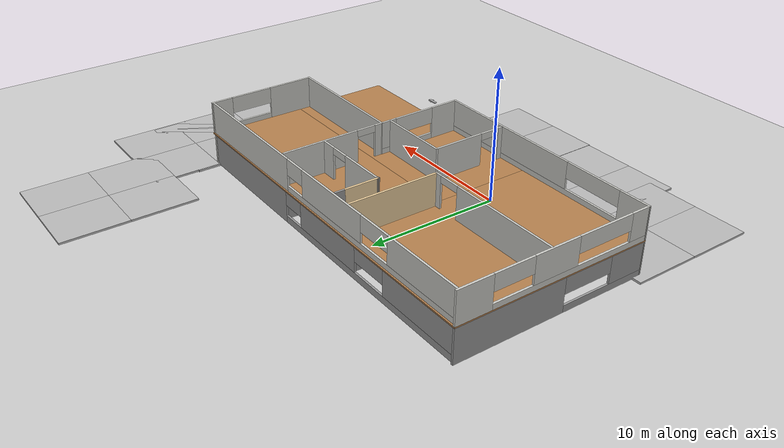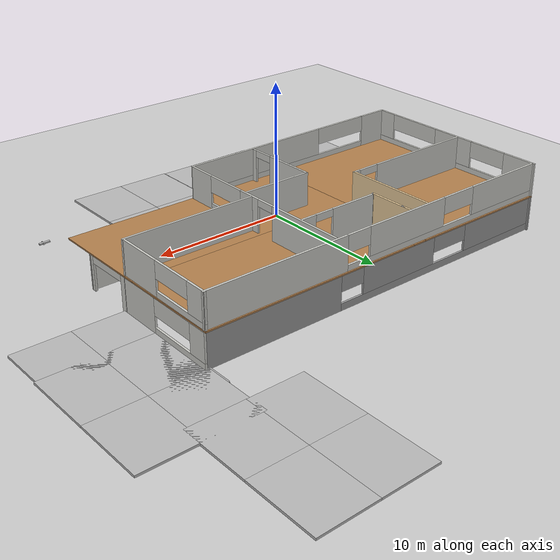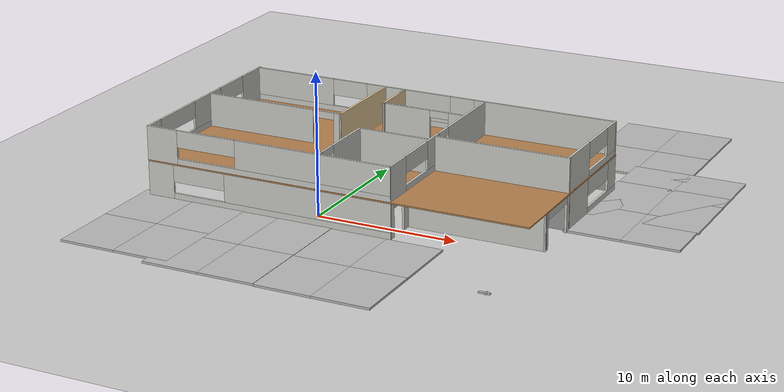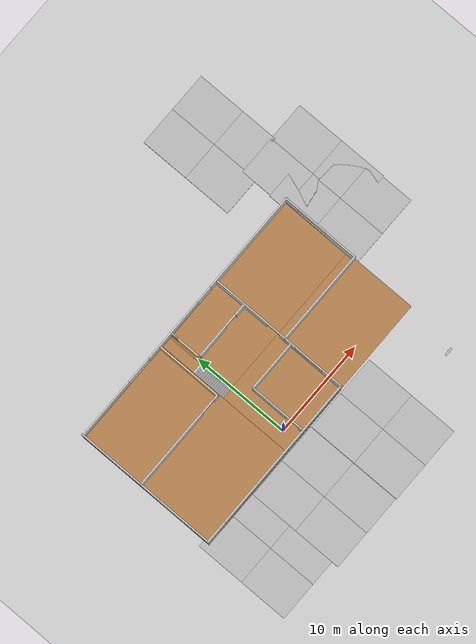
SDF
<sdf version="1.7">
 <world name="default">
  <light name="sun" type="directional">
   <pose>0 0 10 0 -0 0</pose>
   <diffuse>0.8 0.8 0.8 1</diffuse>
   <specular>0.2 0.2 0.2 1</specular>
   <attenuation>
    <range>1000</range>
    <constant>0.9</constant>
    <linear>0.01</linear>
    <quadratic>0.001</quadratic>
   </attenuation>
   <direction>-0.5 0.1 -0.9</direction>
   <spot><inner_angle>0</inner_angle><outer_angle>0</outer_angle><falloff>0</falloff></spot>
  </light>
  <model name="ground_plane">
   <static>1</static>
   <link name="link">
    <collision name="collision">
     <geometry><plane><normal>0 0 1</normal><size>100 100</size></plane></geometry>
     <surface>
      <contact><collide_bitmask>65535</collide_bitmask></contact>
      <friction><ode><mu>100</mu><mu2>50</mu2></ode></friction>
     </surface>
    </collision>
    <visual name="visual">
     <cast_shadows>0</cast_shadows>
     <geometry><plane><normal>0 0 1</normal><size>100 100</size></plane></geometry>
     <material>
      <script><uri>file://media/materials/scripts/gazebo.material</uri><name>Gazebo/Grey</name></script>
     </material>
    </visual>
   </link>
  </model>
  <gravity>0 0 -9.8</gravity>
  <magnetic_field>6e-06 2.3e-05 -4.2e-05</magnetic_field>
  <atmosphere type="adiabatic"/>
  <physics type="ode">
   <max_step_size>0.001</max_step_size>
   <real_time_factor>1</real_time_factor>
   <real_time_update_rate>1000</real_time_update_rate>
  </physics>
  <scene><ambient>0.4 0.4 0.4 1</ambient><background>0.7 0.7 0.7 1</background><shadows>1</shadows></scene>
  <spherical_coordinates>
   <surface_model>EARTH_WGS84</surface_model>
   <latitude_deg>0</latitude_deg>
   <longitude_deg>0</longitude_deg>
   <elevation>0</elevation>
   <heading_deg>0</heading_deg>
  </spherical_coordinates>
  <model name="my_house">
   <pose>1.85305 5.78303 0 0 -0 0</pose>
   <link name="Floor_0">
    <pose>-0.014814 -0 2.5 0 -0 0</pose>
    <visual name="Floor_0_Visual_0">
     <pose>-8.5815 0 0.05 0 -0 0</pose>
     <geometry><box><size>10.7164 14.8085 0.1</size></box></geometry>
     <material>
      <script><uri>file://media/materials/scripts/gazebo.material</uri><name>Gazebo/Wood</name></script>
      <ambient>1 1 1 1</ambient>
     </material>
     <meta><layer>1</layer></meta>
    </visual>
    <collision name="Floor_0_Collision_0">
     <geometry><box><size>10.7164 14.8085 0.1</size></box></geometry>
     <pose>-8.5815 0 0.05 0 -0 0</pose>
    </collision>
    <visual name="Floor_0_Visual_1">
     <pose>5.35818 -3.65615 0.05 0 -0 0</pose>
     <geometry><box><size>17.163 7.49614 0.1</size></box></geometry>
     <material>
      <script><uri>file://media/materials/scripts/gazebo.material</uri><name>Gazebo/Wood</name></script>
      <ambient>1 1 1 1</ambient>
     </material>
     <meta><layer>1</layer></meta>
    </visual>
    <collision name="Floor_0_Collision_1">
     <geometry><box><size>17.163 7.49614 0.1</size></box></geometry>
     <pose>5.35818 -3.65615 0.05 0 -0 0</pose>
    </collision>
    <visual name="Floor_0_Visual_2">
     <pose>5.87276 3.74807 0.05 0 -0 0</pose>
     <geometry><box><size>16.1338 7.31231 0.1</size></box></geometry>
     <material>
      <script><uri>file://media/materials/scripts/gazebo.material</uri><name>Gazebo/Wood</name></script>
      <ambient>1 1 1 1</ambient>
     </material>
     <meta><layer>1</layer></meta>
    </visual>
    <collision name="Floor_0_Collision_2">
     <geometry><box><size>16.1338 7.31231 0.1</size></box></geometry>
     <pose>5.87276 3.74807 0.05 0 -0 0</pose>
    </collision>
    <visual name="Floor_0_Visual_3">
     <pose>-2.70874 5.51265 0.05 0 -0 0</pose>
     <geometry><box><size>1.02917 3.78314 0.1</size></box></geometry>
     <material>
      <script><uri>file://media/materials/scripts/gazebo.material</uri><name>Gazebo/Wood</name></script>
      <ambient>1 1 1 1</ambient>
     </material>
     <meta><layer>1</layer></meta>
    </visual>
    <collision name="Floor_0_Collision_3">
     <geometry><box><size>1.02917 3.78314 0.1</size></box></geometry>
     <pose>-2.70874 5.51265 0.05 0 -0 0</pose>
    </collision>
   </link>
   <link name="Stairs_0">
    <visual name="Stairs_0_Visual_0">
     <pose>-2.72356 3.50345 0.083333 0 -0 0</pose>
     <geometry><box><size>1.02917 0.235278 0.166667</size></box></geometry>
     <material>
      <script><uri>file://media/materials/scripts/gazebo.material</uri><name>Gazebo/Grey</name></script>
      <ambient>1 1 1 1</ambient>
     </material>
     <meta><layer>0</layer></meta>
    </visual>
    <collision name="Stairs_0_Collision_0">
     <geometry><box><size>1.02917 0.235278 0.166667</size></box></geometry>
     <pose>-2.72356 3.50345 0.083333 0 -0 0</pose>
    </collision>
    <visual name="Stairs_0_Visual_1">
     <pose>-2.72356 3.26817 0.25 0 -0 0</pose>
     <geometry><box><size>1.02917 0.235278 0.166667</size></box></geometry>
     <material>
      <script><uri>file://media/materials/scripts/gazebo.material</uri><name>Gazebo/Grey</name></script>
      <ambient>1 1 1 1</ambient>
     </material>
     <meta><layer>0</layer></meta>
    </visual>
    <collision name="Stairs_0_Collision_1">
     <geometry><box><size>1.02917 0.235278 0.166667</size></box></geometry>
     <pose>-2.72356 3.26817 0.25 0 -0 0</pose>
    </collision>
    <visual name="Stairs_0_Visual_2">
     <pose>-2.72356 3.03289 0.416667 0 -0 0</pose>
     <geometry><box><size>1.02917 0.235278 0.166667</size></box></geometry>
     <material>
      <script><uri>file://media/materials/scripts/gazebo.material</uri><name>Gazebo/Grey</name></script>
      <ambient>1 1 1 1</ambient>
     </material>
     <meta><layer>0</layer></meta>
    </visual>
    <collision name="Stairs_0_Collision_2">
     <geometry><box><size>1.02917 0.235278 0.166667</size></box></geometry>
     <pose>-2.72356 3.03289 0.416667 0 -0 0</pose>
    </collision>
    <visual name="Stairs_0_Visual_3">
     <pose>-2.72356 2.79761 0.583333 0 -0 0</pose>
     <geometry><box><size>1.02917 0.235278 0.166667</size></box></geometry>
     <material>
      <script><uri>file://media/materials/scripts/gazebo.material</uri><name>Gazebo/Grey</name></script>
      <ambient>1 1 1 1</ambient>
     </material>
     <meta><layer>0</layer></meta>
    </visual>
    <collision name="Stairs_0_Collision_3">
     <geometry><box><size>1.02917 0.235278 0.166667</size></box></geometry>
     <pose>-2.72356 2.79761 0.583333 0 -0 0</pose>
    </collision>
    <visual name="Stairs_0_Visual_4">
     <pose>-2.72356 2.56233 0.75 0 -0 0</pose>
     <geometry><box><size>1.02917 0.235278 0.166667</size></box></geometry>
     <material>
      <script><uri>file://media/materials/scripts/gazebo.material</uri><name>Gazebo/Grey</name></script>
      <ambient>1 1 1 1</ambient>
     </material>
     <meta><layer>0</layer></meta>
    </visual>
    <collision name="Stairs_0_Collision_4">
     <geometry><box><size>1.02917 0.235278 0.166667</size></box></geometry>
     <pose>-2.72356 2.56233 0.75 0 -0 0</pose>
    </collision>
    <visual name="Stairs_0_Visual_5">
     <pose>-2.72356 2.32706 0.916667 0 -0 0</pose>
     <geometry><box><size>1.02917 0.235278 0.166667</size></box></geometry>
     <material>
      <script><uri>file://media/materials/scripts/gazebo.material</uri><name>Gazebo/Grey</name></script>
      <ambient>1 1 1 1</ambient>
     </material>
     <meta><layer>0</layer></meta>
    </visual>
    <collision name="Stairs_0_Collision_5">
     <geometry><box><size>1.02917 0.235278 0.166667</size></box></geometry>
     <pose>-2.72356 2.32706 0.916667 0 -0 0</pose>
    </collision>
    <visual name="Stairs_0_Visual_6">
     <pose>-2.72356 2.09178 1.08333 0 -0 0</pose>
     <geometry><box><size>1.02917 0.235278 0.166667</size></box></geometry>
     <material>
      <script><uri>file://media/materials/scripts/gazebo.material</uri><name>Gazebo/Grey</name></script>
      <ambient>1 1 1 1</ambient>
     </material>
     <meta><layer>0</layer></meta>
    </visual>
    <collision name="Stairs_0_Collision_6">
     <geometry><box><size>1.02917 0.235278 0.166667</size></box></geometry>
     <pose>-2.72356 2.09178 1.08333 0 -0 0</pose>
    </collision>
    <visual name="Stairs_0_Visual_7">
     <pose>-2.72356 1.8565 1.25 0 -0 0</pose>
     <geometry><box><size>1.02917 0.235278 0.166667</size></box></geometry>
     <material>
      <script><uri>file://media/materials/scripts/gazebo.material</uri><name>Gazebo/Grey</name></script>
      <ambient>1 1 1 1</ambient>
     </material>
     <meta><layer>0</layer></meta>
    </visual>
    <collision name="Stairs_0_Collision_7">
     <geometry><box><size>1.02917 0.235278 0.166667</size></box></geometry>
     <pose>-2.72356 1.8565 1.25 0 -0 0</pose>
    </collision>
    <visual name="Stairs_0_Visual_8">
     <pose>-2.72356 1.62122 1.41667 0 -0 0</pose>
     <geometry><box><size>1.02917 0.235278 0.166667</size></box></geometry>
     <material>
      <script><uri>file://media/materials/scripts/gazebo.material</uri><name>Gazebo/Grey</name></script>
      <ambient>1 1 1 1</ambient>
     </material>
     <meta><layer>0</layer></meta>
    </visual>
    <collision name="Stairs_0_Collision_8">
     <geometry><box><size>1.02917 0.235278 0.166667</size></box></geometry>
     <pose>-2.72356 1.62122 1.41667 0 -0 0</pose>
    </collision>
    <visual name="Stairs_0_Visual_9">
     <pose>-2.72356 1.38594 1.58333 0 -0 0</pose>
     <geometry><box><size>1.02917 0.235278 0.166667</size></box></geometry>
     <material>
      <script><uri>file://media/materials/scripts/gazebo.material</uri><name>Gazebo/Grey</name></script>
      <ambient>1 1 1 1</ambient>
     </material>
     <meta><layer>0</layer></meta>
    </visual>
    <collision name="Stairs_0_Collision_9">
     <geometry><box><size>1.02917 0.235278 0.166667</size></box></geometry>
     <pose>-2.72356 1.38594 1.58333 0 -0 0</pose>
    </collision>
    <visual name="Stairs_0_Visual_10">
     <pose>-2.72356 1.15067 1.75 0 -0 0</pose>
     <geometry><box><size>1.02917 0.235278 0.166667</size></box></geometry>
     <material>
      <script><uri>file://media/materials/scripts/gazebo.material</uri><name>Gazebo/Grey</name></script>
      <ambient>1 1 1 1</ambient>
     </material>
     <meta><layer>0</layer></meta>
    </visual>
    <collision name="Stairs_0_Collision_10">
     <geometry><box><size>1.02917 0.235278 0.166667</size></box></geometry>
     <pose>-2.72356 1.15067 1.75 0 -0 0</pose>
    </collision>
    <visual name="Stairs_0_Visual_11">
     <pose>-2.72356 0.91539 1.91667 0 -0 0</pose>
     <geometry><box><size>1.02917 0.235278 0.166667</size></box></geometry>
     <material>
      <script><uri>file://media/materials/scripts/gazebo.material</uri><name>Gazebo/Grey</name></script>
      <ambient>1 1 1 1</ambient>
     </material>
     <meta><layer>0</layer></meta>
    </visual>
    <collision name="Stairs_0_Collision_11">
     <geometry><box><size>1.02917 0.235278 0.166667</size></box></geometry>
     <pose>-2.72356 0.91539 1.91667 0 -0 0</pose>
    </collision>
    <visual name="Stairs_0_Visual_12">
     <pose>-2.72356 0.680112 2.08333 0 -0 0</pose>
     <geometry><box><size>1.02917 0.235278 0.166667</size></box></geometry>
     <material>
      <script><uri>file://media/materials/scripts/gazebo.material</uri><name>Gazebo/Grey</name></script>
      <ambient>1 1 1 1</ambient>
     </material>
     <meta><layer>0</layer></meta>
    </visual>
    <collision name="Stairs_0_Collision_12">
     <geometry><box><size>1.02917 0.235278 0.166667</size></box></geometry>
     <pose>-2.72356 0.680112 2.08333 0 -0 0</pose>
    </collision>
    <visual name="Stairs_0_Visual_13">
     <pose>-2.72356 0.444834 2.25 0 -0 0</pose>
     <geometry><box><size>1.02917 0.235278 0.166667</size></box></geometry>
     <material>
      <script><uri>file://media/materials/scripts/gazebo.material</uri><name>Gazebo/Grey</name></script>
      <ambient>1 1 1 1</ambient>
     </material>
     <meta><layer>0</layer></meta>
    </visual>
    <collision name="Stairs_0_Collision_13">
     <geometry><box><size>1.02917 0.235278 0.166667</size></box></geometry>
     <pose>-2.72356 0.444834 2.25 0 -0 0</pose>
    </collision>
    <visual name="Stairs_0_Visual_14">
     <pose>-2.72356 0.209557 2.41667 0 -0 0</pose>
     <geometry><box><size>1.02917 0.235278 0.166667</size></box></geometry>
     <material>
      <script><uri>file://media/materials/scripts/gazebo.material</uri><name>Gazebo/Grey</name></script>
      <ambient>1 1 1 1</ambient>
     </material>
     <meta><layer>0</layer></meta>
    </visual>
    <collision name="Stairs_0_Collision_14">
     <geometry><box><size>1.02917 0.235278 0.166667</size></box></geometry>
     <pose>-2.72356 0.209557 2.41667 0 -0 0</pose>
    </collision>
   </link>
   <link name="Wall_11">
    <pose>-13.8794 0.029226 0 0 -0 -1.5708</pose>
    <visual name="Wall_11_Visual_0">
     <pose>-3.26077 0 1.25 0 -0 0</pose>
     <geometry><box><size>8.22847 0.15 2.5</size></box></geometry>
     <material>
      <script><uri>file://media/materials/scripts/gazebo.material</uri><name>Gazebo/Grey</name></script>
      <ambient>1 1 1 1</ambient>
     </material>
     <meta><layer>0</layer></meta>
    </visual>
    <collision name="Wall_11_Collision_0">
     <geometry><box><size>8.22847 0.15 2.5</size></box></geometry>
     <pose>-3.26077 0 1.25 0 -0 0</pose>
    </collision>
    <visual name="Wall_11_Visual_1">
     <pose>4.11423 0 0.25 0 -0 0</pose>
     <geometry><box><size>6.52153 0.15 0.5</size></box></geometry>
     <material>
      <script><uri>file://media/materials/scripts/gazebo.material</uri><name>Gazebo/Grey</name></script>
      <ambient>1 1 1 1</ambient>
     </material>
     <meta><layer>0</layer></meta>
    </visual>
    <collision name="Wall_11_Collision_1">
     <geometry><box><size>6.52153 0.15 0.5</size></box></geometry>
     <pose>4.11423 0 0.25 0 -0 0</pose>
    </collision>
    <visual name="Wall_11_Visual_2">
     <pose>5.98709 0 1.5 0 -0 0</pose>
     <geometry><box><size>2.77581 0.15 2</size></box></geometry>
     <material>
      <script><uri>file://media/materials/scripts/gazebo.material</uri><name>Gazebo/Grey</name></script>
      <ambient>1 1 1 1</ambient>
     </material>
     <meta><layer>0</layer></meta>
    </visual>
    <collision name="Wall_11_Collision_2">
     <geometry><box><size>2.77581 0.15 2</size></box></geometry>
     <pose>5.98709 0 1.5 0 -0 0</pose>
    </collision>
    <visual name="Wall_11_Visual_3">
     <pose>2.72633 0 1.9 0 -0 0</pose>
     <geometry><box><size>3.74572 0.15 1.2</size></box></geometry>
     <material>
      <script><uri>file://media/materials/scripts/gazebo.material</uri><name>Gazebo/Grey</name></script>
      <ambient>1 1 1 1</ambient>
     </material>
     <meta><layer>0</layer></meta>
    </visual>
    <collision name="Wall_11_Collision_3">
     <geometry><box><size>3.74572 0.15 1.2</size></box></geometry>
     <pose>2.72633 0 1.9 0 -0 0</pose>
    </collision>
   </link>
   <link name="Wall_12">
    <pose>-4.82938 -7.31452 0 0 -0 0.001611</pose>
    <visual name="Wall_12_Visual_0">
     <pose>-8.14277 0 1.25 0 -0 0</pose>
     <geometry><box><size>1.96449 0.15 2.5</size></box></geometry>
     <material>
      <script><uri>file://media/materials/scripts/gazebo.material</uri><name>Gazebo/CeilingTiled</name></script>
      <ambient>0.760784 0.662745 0.627451 1</ambient>
     </material>
     <meta><layer>0</layer></meta>
    </visual>
    <collision name="Wall_12_Collision_0">
     <geometry><box><size>1.96449 0.15 2.5</size></box></geometry>
     <pose>-8.14277 0 1.25 0 -0 0</pose>
    </collision>
    <visual name="Wall_12_Visual_1">
     <pose>0.982245 0 0.25 0 -0 0</pose>
     <geometry><box><size>16.2855 0.15 0.5</size></box></geometry>
     <material>
      <script><uri>file://media/materials/scripts/gazebo.material</uri><name>Gazebo/CeilingTiled</name></script>
      <ambient>0.760784 0.662745 0.627451 1</ambient>
     </material>
     <meta><layer>0</layer></meta>
    </visual>
    <collision name="Wall_12_Collision_1">
     <geometry><box><size>16.2855 0.15 0.5</size></box></geometry>
     <pose>0.982245 0 0.25 0 -0 0</pose>
    </collision>
    <visual name="Wall_12_Visual_2">
     <pose>2.94253 0 1.5 0 -0 0</pose>
     <geometry><box><size>12.365 0.15 2</size></box></geometry>
     <material>
      <script><uri>file://media/materials/scripts/gazebo.material</uri><name>Gazebo/CeilingTiled</name></script>
      <ambient>0.760784 0.662745 0.627451 1</ambient>
     </material>
     <meta><layer>0</layer></meta>
    </visual>
    <collision name="Wall_12_Collision_2">
     <geometry><box><size>12.365 0.15 2</size></box></geometry>
     <pose>2.94253 0 1.5 0 -0 0</pose>
    </collision>
    <visual name="Wall_12_Visual_3">
     <pose>-5.20024 0 1.9 0 -0 0</pose>
     <geometry><box><size>3.92057 0.15 1.2</size></box></geometry>
     <material>
      <script><uri>file://media/materials/scripts/gazebo.material</uri><name>Gazebo/CeilingTiled</name></script>
      <ambient>0.760784 0.662745 0.627451 1</ambient>
     </material>
     <meta><layer>0</layer></meta>
    </visual>
    <collision name="Wall_12_Collision_3">
     <geometry><box><size>3.92057 0.15 1.2</size></box></geometry>
     <pose>-5.20024 0 1.9 0 -0 0</pose>
    </collision>
   </link>
   <link name="Wall_13">
    <pose>4.22062 -4.04369 0 0 -0 1.5708</pose>
    <visual name="Wall_13_Visual_0">
     <pose>-3.02669 0 1.25 0 -0 0</pose>
     <geometry><box><size>0.492455 0.15 2.5</size></box></geometry>
     <material>
      <script><uri>file://media/materials/scripts/gazebo.material</uri><name>Gazebo/CeilingTiled</name></script>
      <ambient>0.760784 0.662745 0.627451 1</ambient>
     </material>
     <meta><layer>0</layer></meta>
    </visual>
    <collision name="Wall_13_Collision_0">
     <geometry><box><size>0.492455 0.15 2.5</size></box></geometry>
     <pose>-3.02669 0 1.25 0 -0 0</pose>
    </collision>
    <visual name="Wall_13_Visual_1">
     <pose>0.929552 0 1.25 0 -0 0</pose>
     <geometry><box><size>4.68674 0.15 2.5</size></box></geometry>
     <material>
      <script><uri>file://media/materials/scripts/gazebo.material</uri><name>Gazebo/CeilingTiled</name></script>
      <ambient>0.760784 0.662745 0.627451 1</ambient>
     </material>
     <meta><layer>0</layer></meta>
    </visual>
    <collision name="Wall_13_Collision_1">
     <geometry><box><size>4.68674 0.15 2.5</size></box></geometry>
     <pose>0.929552 0 1.25 0 -0 0</pose>
    </collision>
    <visual name="Wall_13_Visual_2">
     <pose>-2.09714 0 2.25 0 -0 0</pose>
     <geometry><box><size>1.36665 0.15 0.5</size></box></geometry>
     <material>
      <script><uri>file://media/materials/scripts/gazebo.material</uri><name>Gazebo/CeilingTiled</name></script>
      <ambient>0.760784 0.662745 0.627451 1</ambient>
     </material>
     <meta><layer>0</layer></meta>
    </visual>
    <collision name="Wall_13_Collision_2">
     <geometry><box><size>1.36665 0.15 0.5</size></box></geometry>
     <pose>-2.09714 0 2.25 0 -0 0</pose>
    </collision>
   </link>
   <link name="Wall_14">
    <collision name="Wall_14_Collision">
     <geometry><box><size>9.7504 0.15 2.5</size></box></geometry>
     <pose>0 0 1.25 0 -0 0</pose>
    </collision>
    <visual name="Wall_14_Visual">
     <pose>0 0 1.25 0 -0 0</pose>
     <geometry><box><size>9.7504 0.15 2.5</size></box></geometry>
     <material>
      <script><uri>file://media/materials/scripts/gazebo.material</uri><name>Gazebo/Grey</name></script>
      <ambient>1 1 1 1</ambient>
     </material>
     <meta><layer>0</layer></meta>
    </visual>
    <pose>9.02062 -0.802019 0 0 -0 -0.003038</pose>
   </link>
   <link name="Wall_15">
    <pose>13.8498 3.19589 0 0 -0 1.56353</pose>
    <visual name="Wall_15_Visual_0">
     <pose>-2.46795 0 1.25 0 -0 0</pose>
     <geometry><box><size>3.23931 0.15 2.5</size></box></geometry>
     <material>
      <script><uri>file://media/materials/scripts/gazebo.material</uri><name>Gazebo/CeilingTiled</name></script>
      <ambient>0.760784 0.662745 0.627451 1</ambient>
     </material>
     <meta><layer>0</layer></meta>
    </visual>
    <collision name="Wall_15_Collision_0">
     <geometry><box><size>3.23931 0.15 2.5</size></box></geometry>
     <pose>-2.46795 0 1.25 0 -0 0</pose>
    </collision>
    <visual name="Wall_15_Visual_1">
     <pose>1.61965 0 0.25 0 -0 0</pose>
     <geometry><box><size>4.9359 0.15 0.5</size></box></geometry>
     <material>
      <script><uri>file://media/materials/scripts/gazebo.material</uri><name>Gazebo/CeilingTiled</name></script>
      <ambient>0.760784 0.662745 0.627451 1</ambient>
     </material>
     <meta><layer>0</layer></meta>
    </visual>
    <collision name="Wall_15_Collision_1">
     <geometry><box><size>4.9359 0.15 0.5</size></box></geometry>
     <pose>1.61965 0 0.25 0 -0 0</pose>
    </collision>
    <visual name="Wall_15_Visual_2">
     <pose>3.38966 0 1.5 0 -0 0</pose>
     <geometry><box><size>1.39589 0.15 2</size></box></geometry>
     <material>
      <script><uri>file://media/materials/scripts/gazebo.material</uri><name>Gazebo/CeilingTiled</name></script>
      <ambient>0.760784 0.662745 0.627451 1</ambient>
     </material>
     <meta><layer>0</layer></meta>
    </visual>
    <collision name="Wall_15_Collision_2">
     <geometry><box><size>1.39589 0.15 2</size></box></geometry>
     <pose>3.38966 0 1.5 0 -0 0</pose>
    </collision>
    <visual name="Wall_15_Visual_3">
     <pose>0.921706 0 1.9 0 -0 0</pose>
     <geometry><box><size>3.54 0.15 1.2</size></box></geometry>
     <material>
      <script><uri>file://media/materials/scripts/gazebo.material</uri><name>Gazebo/CeilingTiled</name></script>
      <ambient>0.760784 0.662745 0.627451 1</ambient>
     </material>
     <meta><layer>0</layer></meta>
    </visual>
    <collision name="Wall_15_Collision_3">
     <geometry><box><size>3.54 0.15 1.2</size></box></geometry>
     <pose>0.921706 0 1.9 0 -0 0</pose>
    </collision>
   </link>
   <link name="Wall_16">
    <pose>0.020624 7.17922 0 0 -0 3.13948</pose>
    <visual name="Wall_16_Visual_0">
     <pose>-8.84249 0 1.25 0 -0 0</pose>
     <geometry><box><size>10.0651 0.15 2.5</size></box></geometry>
     <material>
      <script><uri>file://media/materials/scripts/gazebo.material</uri><name>Gazebo/Grey</name></script>
      <ambient>1 1 1 1</ambient>
     </material>
     <meta><layer>0</layer></meta>
    </visual>
    <collision name="Wall_16_Collision_0">
     <geometry><box><size>10.0651 0.15 2.5</size></box></geometry>
     <pose>-8.84249 0 1.25 0 -0 0</pose>
    </collision>
    <visual name="Wall_16_Visual_1">
     <pose>5.03254 0 0.25 0 -0 0</pose>
     <geometry><box><size>17.685 0.15 0.5</size></box></geometry>
     <material>
      <script><uri>file://media/materials/scripts/gazebo.material</uri><name>Gazebo/Grey</name></script>
      <ambient>1 1 1 1</ambient>
     </material>
     <meta><layer>0</layer></meta>
    </visual>
    <collision name="Wall_16_Collision_1">
     <geometry><box><size>17.685 0.15 0.5</size></box></geometry>
     <pose>5.03254 0 0.25 0 -0 0</pose>
    </collision>
    <visual name="Wall_16_Visual_2">
     <pose>1.13272 0 1.5 0 -0 0</pose>
     <geometry><box><size>6.24364 0.15 2</size></box></geometry>
     <material>
      <script><uri>file://media/materials/scripts/gazebo.material</uri><name>Gazebo/Grey</name></script>
      <ambient>1 1 1 1</ambient>
     </material>
     <meta><layer>0</layer></meta>
    </visual>
    <collision name="Wall_16_Collision_2">
     <geometry><box><size>6.24364 0.15 2</size></box></geometry>
     <pose>1.13272 0 1.5 0 -0 0</pose>
    </collision>
    <visual name="Wall_16_Visual_3">
     <pose>10.5439 0 1.5 0 -0 0</pose>
     <geometry><box><size>6.66225 0.15 2</size></box></geometry>
     <material>
      <script><uri>file://media/materials/scripts/gazebo.material</uri><name>Gazebo/Grey</name></script>
      <ambient>1 1 1 1</ambient>
     </material>
     <meta><layer>0</layer></meta>
    </visual>
    <collision name="Wall_16_Collision_3">
     <geometry><box><size>6.66225 0.15 2</size></box></geometry>
     <pose>10.5439 0 1.5 0 -0 0</pose>
    </collision>
    <visual name="Wall_16_Visual_4">
     <pose>-2.89953 0 1.9 0 -0 0</pose>
     <geometry><box><size>1.82085 0.15 1.2</size></box></geometry>
     <material>
      <script><uri>file://media/materials/scripts/gazebo.material</uri><name>Gazebo/Grey</name></script>
      <ambient>1 1 1 1</ambient>
     </material>
     <meta><layer>0</layer></meta>
    </visual>
    <collision name="Wall_16_Collision_4">
     <geometry><box><size>1.82085 0.15 1.2</size></box></geometry>
     <pose>-2.89953 0 1.9 0 -0 0</pose>
    </collision>
    <visual name="Wall_16_Visual_5">
     <pose>5.73366 0 1.9 0 -0 0</pose>
     <geometry><box><size>2.95825 0.15 1.2</size></box></geometry>
     <material>
      <script><uri>file://media/materials/scripts/gazebo.material</uri><name>Gazebo/Grey</name></script>
      <ambient>1 1 1 1</ambient>
     </material>
     <meta><layer>0</layer></meta>
    </visual>
    <collision name="Wall_16_Collision_5">
     <geometry><box><size>2.95825 0.15 1.2</size></box></geometry>
     <pose>5.73366 0 1.9 0 -0 0</pose>
    </collision>
   </link>
   <link name="Wall_22">
    <collision name="Wall_22_Collision">
     <geometry><box><size>9.75 0.15 2.5</size></box></geometry>
     <pose>0 0 1.25 0 -0 0</pose>
    </collision>
    <visual name="Wall_22_Visual">
     <pose>0 0 1.25 0 -0 0</pose>
     <geometry><box><size>9.75 0.15 2.5</size></box></geometry>
     <material>
      <script><uri>file://media/materials/scripts/gazebo.material</uri><name>Gazebo/CeilingTiled</name></script>
      <ambient>0.760784 0.662745 0.627451 1</ambient>
     </material>
     <meta><layer>0</layer></meta>
    </visual>
    <pose>9.06159 -4.72033 0 0 -0 0</pose>
   </link>
   <link name="Wall_24">
    <pose>13.8411 -2.76847 0 0 -0 1.58129</pose>
    <visual name="Wall_24_Visual_0">
     <pose>-1.82986 0 1.25 0 -0 0</pose>
     <geometry><box><size>0.394219 0.15 2.5</size></box></geometry>
     <material>
      <script><uri>file://media/materials/scripts/gazebo.material</uri><name>Gazebo/CeilingTiled</name></script>
      <ambient>0.760784 0.662745 0.627451 1</ambient>
     </material>
     <meta><layer>0</layer></meta>
    </visual>
    <collision name="Wall_24_Collision_0">
     <geometry><box><size>0.394219 0.15 2.5</size></box></geometry>
     <pose>-1.82986 0 1.25 0 -0 0</pose>
    </collision>
    <visual name="Wall_24_Visual_1">
     <pose>1.77114 0 1.25 0 -0 0</pose>
     <geometry><box><size>0.511651 0.15 2.5</size></box></geometry>
     <material>
      <script><uri>file://media/materials/scripts/gazebo.material</uri><name>Gazebo/CeilingTiled</name></script>
      <ambient>0.760784 0.662745 0.627451 1</ambient>
     </material>
     <meta><layer>0</layer></meta>
    </visual>
    <collision name="Wall_24_Collision_1">
     <geometry><box><size>0.511651 0.15 2.5</size></box></geometry>
     <pose>1.77114 0 1.25 0 -0 0</pose>
    </collision>
    <visual name="Wall_24_Visual_2">
     <pose>-0.058716 0 2.25 0 -0 0</pose>
     <geometry><box><size>3.14807 0.15 0.5</size></box></geometry>
     <material>
      <script><uri>file://media/materials/scripts/gazebo.material</uri><name>Gazebo/CeilingTiled</name></script>
      <ambient>0.760784 0.662745 0.627451 1</ambient>
     </material>
     <meta><layer>0</layer></meta>
    </visual>
    <collision name="Wall_24_Collision_2">
     <geometry><box><size>3.14807 0.15 0.5</size></box></geometry>
     <pose>-0.058716 0 2.25 0 -0 0</pose>
    </collision>
   </link>
   <link name="Wall_26">
    <pose>-8.67521 0.471138 0 0 -0 0</pose>
    <visual name="Wall_26_Visual_0">
     <pose>-0.967881 0 1.25 0 -0 0</pose>
     <geometry><box><size>8.56424 0.15 2.5</size></box></geometry>
     <material>
      <script><uri>file://media/materials/scripts/gazebo.material</uri><name>Gazebo/Grey</name></script>
      <ambient>1 1 1 1</ambient>
     </material>
     <meta><layer>0</layer></meta>
    </visual>
    <collision name="Wall_26_Collision_0">
     <geometry><box><size>8.56424 0.15 2.5</size></box></geometry>
     <pose>-0.967881 0 1.25 0 -0 0</pose>
    </collision>
    <visual name="Wall_26_Visual_1">
     <pose>4.95086 0 1.25 0 -0 0</pose>
     <geometry><box><size>0.598278 0.15 2.5</size></box></geometry>
     <material>
      <script><uri>file://media/materials/scripts/gazebo.material</uri><name>Gazebo/Grey</name></script>
      <ambient>1 1 1 1</ambient>
     </material>
     <meta><layer>0</layer></meta>
    </visual>
    <collision name="Wall_26_Collision_1">
     <geometry><box><size>0.598278 0.15 2.5</size></box></geometry>
     <pose>4.95086 0 1.25 0 -0 0</pose>
    </collision>
    <visual name="Wall_26_Visual_2">
     <pose>3.98298 0 2.25 0 -0 0</pose>
     <geometry><box><size>1.33748 0.15 0.5</size></box></geometry>
     <material>
      <script><uri>file://media/materials/scripts/gazebo.material</uri><name>Gazebo/Grey</name></script>
      <ambient>1 1 1 1</ambient>
     </material>
     <meta><layer>0</layer></meta>
    </visual>
    <collision name="Wall_26_Collision_2">
     <geometry><box><size>1.33748 0.15 0.5</size></box></geometry>
     <pose>3.98298 0 2.25 0 -0 0</pose>
    </collision>
   </link>
   <link name="Wall_27">
    <collision name="Wall_27_Collision">
     <geometry><box><size>6.75 0.15 2.5</size></box></geometry>
     <pose>0 0 1.25 0 -0 0</pose>
    </collision>
    <visual name="Wall_27_Visual">
     <pose>0 0 1.25 0 -0 0</pose>
     <geometry><box><size>6.75 0.15 2.5</size></box></geometry>
     <material>
      <script><uri>file://media/materials/scripts/gazebo.material</uri><name>Gazebo/Grey</name></script>
      <ambient>1 1 1 1</ambient>
     </material>
     <meta><layer>0</layer></meta>
    </visual>
    <pose>-3.50021 3.77114 0 0 -0 1.5708</pose>
   </link>
   <link name="Wall_29">
    <pose>4.22062 3.12298 0 0 -0 1.5708</pose>
    <visual name="Wall_29_Visual_0">
     <pose>-3.68396 0 1.25 0 -0 0</pose>
     <geometry><box><size>0.602909 0.15 2.5</size></box></geometry>
     <material>
      <script><uri>file://media/materials/scripts/gazebo.material</uri><name>Gazebo/Grey</name></script>
      <ambient>1 1 1 1</ambient>
     </material>
     <meta><layer>0</layer></meta>
    </visual>
    <collision name="Wall_29_Collision_0">
     <geometry><box><size>0.602909 0.15 2.5</size></box></geometry>
     <pose>-3.68396 0 1.25 0 -0 0</pose>
    </collision>
    <visual name="Wall_29_Visual_1">
     <pose>0.955613 0 1.25 0 -0 0</pose>
     <geometry><box><size>6.05961 0.15 2.5</size></box></geometry>
     <material>
      <script><uri>file://media/materials/scripts/gazebo.material</uri><name>Gazebo/Grey</name></script>
      <ambient>1 1 1 1</ambient>
     </material>
     <meta><layer>0</layer></meta>
    </visual>
    <collision name="Wall_29_Collision_1">
     <geometry><box><size>6.05961 0.15 2.5</size></box></geometry>
     <pose>0.955613 0 1.25 0 -0 0</pose>
    </collision>
    <visual name="Wall_29_Visual_2">
     <pose>-2.72835 0 2.25 0 -0 0</pose>
     <geometry><box><size>1.30832 0.15 0.5</size></box></geometry>
     <material>
      <script><uri>file://media/materials/scripts/gazebo.material</uri><name>Gazebo/Grey</name></script>
      <ambient>1 1 1 1</ambient>
     </material>
     <meta><layer>0</layer></meta>
    </visual>
    <collision name="Wall_29_Collision_2">
     <geometry><box><size>1.30832 0.15 0.5</size></box></geometry>
     <pose>-2.72835 0 2.25 0 -0 0</pose>
    </collision>
   </link>
   <link name="Wall_33">
    <pose>0.303556 3.91267 0 0 -0 0</pose>
    <visual name="Wall_33_Visual_0">
     <pose>-0.949078 0 1.25 0 -0 0</pose>
     <geometry><box><size>5.85184 0.15 2.5</size></box></geometry>
     <material>
      <script><uri>file://media/materials/scripts/gazebo.material</uri><name>Gazebo/Grey</name></script>
      <ambient>1 1 1 1</ambient>
     </material>
     <meta><layer>0</layer></meta>
    </visual>
    <collision name="Wall_33_Collision_0">
     <geometry><box><size>5.85184 0.15 2.5</size></box></geometry>
     <pose>-0.949078 0 1.25 0 -0 0</pose>
    </collision>
    <visual name="Wall_33_Visual_1">
     <pose>3.5655 0 1.25 0 -0 0</pose>
     <geometry><box><size>0.619005 0.15 2.5</size></box></geometry>
     <material>
      <script><uri>file://media/materials/scripts/gazebo.material</uri><name>Gazebo/Grey</name></script>
      <ambient>1 1 1 1</ambient>
     </material>
     <meta><layer>0</layer></meta>
    </visual>
    <collision name="Wall_33_Collision_1">
     <geometry><box><size>0.619005 0.15 2.5</size></box></geometry>
     <pose>3.5655 0 1.25 0 -0 0</pose>
    </collision>
    <visual name="Wall_33_Visual_2">
     <pose>2.61642 0 2.25 0 -0 0</pose>
     <geometry><box><size>1.27915 0.15 0.5</size></box></geometry>
     <material>
      <script><uri>file://media/materials/scripts/gazebo.material</uri><name>Gazebo/Grey</name></script>
      <ambient>1 1 1 1</ambient>
     </material>
     <meta><layer>0</layer></meta>
    </visual>
    <collision name="Wall_33_Collision_2">
     <geometry><box><size>1.27915 0.15 0.5</size></box></geometry>
     <pose>2.61642 0 2.25 0 -0 0</pose>
    </collision>
   </link>
   <link name="Wall_36">
    <pose>-13.8794 0.029226 2.5 0 -0 -1.5708</pose>
    <visual name="Wall_36_Visual_0">
     <pose>-6.06255 0 1.25 0 -0 0</pose>
     <geometry><box><size>2.62491 0.15 2.5</size></box></geometry>
     <material>
      <script><uri>file://media/materials/scripts/gazebo.material</uri><name>Gazebo/CeilingTiled</name></script>
      <ambient>0.921569 0.807843 0.615686 1</ambient>
     </material>
     <meta><layer>1</layer></meta>
    </visual>
    <collision name="Wall_36_Collision_0">
     <geometry><box><size>2.62491 0.15 2.5</size></box></geometry>
     <pose>-6.06255 0 1.25 0 -0 0</pose>
    </collision>
    <visual name="Wall_36_Visual_1">
     <pose>1.31245 0 0.25 0 -0 0</pose>
     <geometry><box><size>12.1251 0.15 0.5</size></box></geometry>
     <material>
      <script><uri>file://media/materials/scripts/gazebo.material</uri><name>Gazebo/CeilingTiled</name></script>
      <ambient>0.921569 0.807843 0.615686 1</ambient>
     </material>
     <meta><layer>1</layer></meta>
    </visual>
    <collision name="Wall_36_Collision_1">
     <geometry><box><size>12.1251 0.15 0.5</size></box></geometry>
     <pose>1.31245 0 0.25 0 -0 0</pose>
    </collision>
    <visual name="Wall_36_Visual_2">
     <pose>-0.048177 0 1.5 0 -0 0</pose>
     <geometry><box><size>3.429 0.15 2</size></box></geometry>
     <material>
      <script><uri>file://media/materials/scripts/gazebo.material</uri><name>Gazebo/CeilingTiled</name></script>
      <ambient>0.921569 0.807843 0.615686 1</ambient>
     </material>
     <meta><layer>1</layer></meta>
    </visual>
    <collision name="Wall_36_Collision_2">
     <geometry><box><size>3.429 0.15 2</size></box></geometry>
     <pose>-0.048177 0 1.5 0 -0 0</pose>
    </collision>
    <visual name="Wall_36_Visual_3">
     <pose>6.65601 0 1.5 0 -0 0</pose>
     <geometry><box><size>1.43798 0.15 2</size></box></geometry>
     <material>
      <script><uri>file://media/materials/scripts/gazebo.material</uri><name>Gazebo/CeilingTiled</name></script>
      <ambient>0.921569 0.807843 0.615686 1</ambient>
     </material>
     <meta><layer>1</layer></meta>
    </visual>
    <collision name="Wall_36_Collision_3">
     <geometry><box><size>1.43798 0.15 2</size></box></geometry>
     <pose>6.65601 0 1.5 0 -0 0</pose>
    </collision>
    <visual name="Wall_36_Visual_4">
     <pose>-3.25639 0 1.9 0 -0 0</pose>
     <geometry><box><size>2.98742 0.15 1.2</size></box></geometry>
     <material>
      <script><uri>file://media/materials/scripts/gazebo.material</uri><name>Gazebo/CeilingTiled</name></script>
      <ambient>0.921569 0.807843 0.615686 1</ambient>
     </material>
     <meta><layer>1</layer></meta>
    </visual>
    <collision name="Wall_36_Collision_4">
     <geometry><box><size>2.98742 0.15 1.2</size></box></geometry>
     <pose>-3.25639 0 1.9 0 -0 0</pose>
    </collision>
    <visual name="Wall_36_Visual_5">
     <pose>3.80167 0 1.9 0 -0 0</pose>
     <geometry><box><size>4.2707 0.15 1.2</size></box></geometry>
     <material>
      <script><uri>file://media/materials/scripts/gazebo.material</uri><name>Gazebo/CeilingTiled</name></script>
      <ambient>0.921569 0.807843 0.615686 1</ambient>
     </material>
     <meta><layer>1</layer></meta>
    </visual>
    <collision name="Wall_36_Collision_5">
     <geometry><box><size>4.2707 0.15 1.2</size></box></geometry>
     <pose>3.80167 0 1.9 0 -0 0</pose>
    </collision>
   </link>
   <link name="Wall_37">
    <pose>-4.82938 -7.31452 2.5 0 -0 0.001611</pose>
    <visual name="Wall_37_Visual_0">
     <pose>-7.9606 0 1.25 0 -0 0</pose>
     <geometry><box><size>2.32882 0.15 2.5</size></box></geometry>
     <material>
      <script><uri>file://media/materials/scripts/gazebo.material</uri><name>Gazebo/CeilingTiled</name></script>
      <ambient>0.921569 0.807843 0.615686 1</ambient>
     </material>
     <meta><layer>1</layer></meta>
    </visual>
    <collision name="Wall_37_Collision_0">
     <geometry><box><size>2.32882 0.15 2.5</size></box></geometry>
     <pose>-7.9606 0 1.25 0 -0 0</pose>
    </collision>
    <visual name="Wall_37_Visual_1">
     <pose>1.16441 0 0.25 0 -0 0</pose>
     <geometry><box><size>15.9212 0.15 0.5</size></box></geometry>
     <material>
      <script><uri>file://media/materials/scripts/gazebo.material</uri><name>Gazebo/CeilingTiled</name></script>
      <ambient>0.921569 0.807843 0.615686 1</ambient>
     </material>
     <meta><layer>1</layer></meta>
    </visual>
    <collision name="Wall_37_Collision_1">
     <geometry><box><size>15.9212 0.15 0.5</size></box></geometry>
     <pose>1.16441 0 0.25 0 -0 0</pose>
    </collision>
    <visual name="Wall_37_Visual_2">
     <pose>3.3873 0 1.5 0 -0 0</pose>
     <geometry><box><size>11.4754 0.15 2</size></box></geometry>
     <material>
      <script><uri>file://media/materials/scripts/gazebo.material</uri><name>Gazebo/CeilingTiled</name></script>
      <ambient>0.921569 0.807843 0.615686 1</ambient>
     </material>
     <meta><layer>1</layer></meta>
    </visual>
    <collision name="Wall_37_Collision_2">
     <geometry><box><size>11.4754 0.15 2</size></box></geometry>
     <pose>3.3873 0 1.5 0 -0 0</pose>
    </collision>
    <visual name="Wall_37_Visual_3">
     <pose>-4.5733 0 1.9 0 -0 0</pose>
     <geometry><box><size>4.44578 0.15 1.2</size></box></geometry>
     <material>
      <script><uri>file://media/materials/scripts/gazebo.material</uri><name>Gazebo/CeilingTiled</name></script>
      <ambient>0.921569 0.807843 0.615686 1</ambient>
     </material>
     <meta><layer>1</layer></meta>
    </visual>
    <collision name="Wall_37_Collision_3">
     <geometry><box><size>4.44578 0.15 1.2</size></box></geometry>
     <pose>-4.5733 0 1.9 0 -0 0</pose>
    </collision>
   </link>
   <link name="Wall_38">
    <pose>4.22062 -4.04369 2.5 0 -0 1.5708</pose>
    <visual name="Wall_38_Visual_0">
     <pose>-2.18936 0 1.25 0 -0 0</pose>
     <geometry><box><size>2.16711 0.15 2.5</size></box></geometry>
     <material>
      <script><uri>file://media/materials/scripts/gazebo.material</uri><name>Gazebo/CeilingTiled</name></script>
      <ambient>0.921569 0.807843 0.615686 1</ambient>
     </material>
     <meta><layer>1</layer></meta>
    </visual>
    <collision name="Wall_38_Collision_0">
     <geometry><box><size>2.16711 0.15 2.5</size></box></geometry>
     <pose>-2.18936 0 1.25 0 -0 0</pose>
    </collision>
    <visual name="Wall_38_Visual_1">
     <pose>1.08356 0 0.25 0 -0 0</pose>
     <geometry><box><size>4.37873 0.15 0.5</size></box></geometry>
     <material>
      <script><uri>file://media/materials/scripts/gazebo.material</uri><name>Gazebo/CeilingTiled</name></script>
      <ambient>0.921569 0.807843 0.615686 1</ambient>
     </material>
     <meta><layer>1</layer></meta>
    </visual>
    <collision name="Wall_38_Collision_1">
     <geometry><box><size>4.37873 0.15 0.5</size></box></geometry>
     <pose>1.08356 0 0.25 0 -0 0</pose>
    </collision>
    <visual name="Wall_38_Visual_2">
     <pose>2.66476 0 1.5 0 -0 0</pose>
     <geometry><box><size>1.21632 0.15 2</size></box></geometry>
     <material>
      <script><uri>file://media/materials/scripts/gazebo.material</uri><name>Gazebo/CeilingTiled</name></script>
      <ambient>0.921569 0.807843 0.615686 1</ambient>
     </material>
     <meta><layer>1</layer></meta>
    </visual>
    <collision name="Wall_38_Collision_2">
     <geometry><box><size>1.21632 0.15 2</size></box></geometry>
     <pose>2.66476 0 1.5 0 -0 0</pose>
    </collision>
    <visual name="Wall_38_Visual_3">
     <pose>0.475398 0 1.9 0 -0 0</pose>
     <geometry><box><size>3.16241 0.15 1.2</size></box></geometry>
     <material>
      <script><uri>file://media/materials/scripts/gazebo.material</uri><name>Gazebo/CeilingTiled</name></script>
      <ambient>0.921569 0.807843 0.615686 1</ambient>
     </material>
     <meta><layer>1</layer></meta>
    </visual>
    <collision name="Wall_38_Collision_3">
     <geometry><box><size>3.16241 0.15 1.2</size></box></geometry>
     <pose>0.475398 0 1.9 0 -0 0</pose>
    </collision>
   </link>
   <link name="Wall_39">
    <collision name="Wall_39_Collision">
     <geometry><box><size>9.72083 0.15 2.5</size></box></geometry>
     <pose>0 0 1.25 0 -0 0</pose>
    </collision>
    <visual name="Wall_39_Visual">
     <pose>0 0 1.25 0 -0 0</pose>
     <geometry><box><size>9.72083 0.15 2.5</size></box></geometry>
     <material>
      <script><uri>file://media/materials/scripts/gazebo.material</uri><name>Gazebo/CeilingTiled</name></script>
      <ambient>0.921569 0.807843 0.615686 1</ambient>
     </material>
     <meta><layer>1</layer></meta>
    </visual>
    <pose>9.00604 -0.787437 2.5 0 -0 0</pose>
   </link>
   <link name="Wall_40">
    <pose>13.7915 3.28339 2.5 0 -0 1.56353</pose>
    <visual name="Wall_40_Visual_0">
     <pose>-2.38067 0 1.25 0 -0 0</pose>
     <geometry><box><size>3.41387 0.15 2.5</size></box></geometry>
     <material>
      <script><uri>file://media/materials/scripts/gazebo.material</uri><name>Gazebo/CeilingTiled</name></script>
      <ambient>1 1 1 1</ambient>
     </material>
     <meta><layer>1</layer></meta>
    </visual>
    <collision name="Wall_40_Collision_0">
     <geometry><box><size>3.41387 0.15 2.5</size></box></geometry>
     <pose>-2.38067 0 1.25 0 -0 0</pose>
    </collision>
    <visual name="Wall_40_Visual_1">
     <pose>1.70694 0 0.25 0 -0 0</pose>
     <geometry><box><size>4.76133 0.15 0.5</size></box></geometry>
     <material>
      <script><uri>file://media/materials/scripts/gazebo.material</uri><name>Gazebo/CeilingTiled</name></script>
      <ambient>1 1 1 1</ambient>
     </material>
     <meta><layer>1</layer></meta>
    </visual>
    <collision name="Wall_40_Collision_1">
     <geometry><box><size>4.76133 0.15 0.5</size></box></geometry>
     <pose>1.70694 0 0.25 0 -0 0</pose>
    </collision>
    <visual name="Wall_40_Visual_2">
     <pose>3.27321 0 1.5 0 -0 0</pose>
     <geometry><box><size>1.62879 0.15 2</size></box></geometry>
     <material>
      <script><uri>file://media/materials/scripts/gazebo.material</uri><name>Gazebo/CeilingTiled</name></script>
      <ambient>1 1 1 1</ambient>
     </material>
     <meta><layer>1</layer></meta>
    </visual>
    <collision name="Wall_40_Collision_2">
     <geometry><box><size>1.62879 0.15 2</size></box></geometry>
     <pose>3.27321 0 1.5 0 -0 0</pose>
    </collision>
    <visual name="Wall_40_Visual_3">
     <pose>0.892541 0 1.9 0 -0 0</pose>
     <geometry><box><size>3.13255 0.15 1.2</size></box></geometry>
     <material>
      <script><uri>file://media/materials/scripts/gazebo.material</uri><name>Gazebo/CeilingTiled</name></script>
      <ambient>1 1 1 1</ambient>
     </material>
     <meta><layer>1</layer></meta>
    </visual>
    <collision name="Wall_40_Collision_3">
     <geometry><box><size>3.13255 0.15 1.2</size></box></geometry>
     <pose>0.892541 0 1.9 0 -0 0</pose>
    </collision>
   </link>
   <link name="Wall_41">
    <pose>0.035206 7.22297 2.5 0 -0 -3.14054</pose>
    <visual name="Wall_41_Visual_0">
     <pose>-8.63955 0 1.25 0 -0 0</pose>
     <geometry><box><size>10.5001 0.15 2.5</size></box></geometry>
     <material>
      <script><uri>file://media/materials/scripts/gazebo.material</uri><name>Gazebo/CeilingTiled</name></script>
      <ambient>0.921569 0.807843 0.615686 1</ambient>
     </material>
     <meta><layer>1</layer></meta>
    </visual>
    <collision name="Wall_41_Collision_0">
     <geometry><box><size>10.5001 0.15 2.5</size></box></geometry>
     <pose>-8.63955 0 1.25 0 -0 0</pose>
    </collision>
    <visual name="Wall_41_Visual_1">
     <pose>5.25004 0 0.25 0 -0 0</pose>
     <geometry><box><size>17.2791 0.15 0.5</size></box></geometry>
     <material>
      <script><uri>file://media/materials/scripts/gazebo.material</uri><name>Gazebo/CeilingTiled</name></script>
      <ambient>0.921569 0.807843 0.615686 1</ambient>
     </material>
     <meta><layer>1</layer></meta>
    </visual>
    <collision name="Wall_41_Collision_1">
     <geometry><box><size>17.2791 0.15 0.5</size></box></geometry>
     <pose>5.25004 0 0.25 0 -0 0</pose>
    </collision>
    <visual name="Wall_41_Visual_2">
     <pose>1.71093 0 1.5 0 -0 0</pose>
     <geometry><box><size>6.55918 0.15 2</size></box></geometry>
     <material>
      <script><uri>file://media/materials/scripts/gazebo.material</uri><name>Gazebo/CeilingTiled</name></script>
      <ambient>0.921569 0.807843 0.615686 1</ambient>
     </material>
     <meta><layer>1</layer></meta>
    </visual>
    <collision name="Wall_41_Collision_2">
     <geometry><box><size>6.55918 0.15 2</size></box></geometry>
     <pose>1.71093 0 1.5 0 -0 0</pose>
    </collision>
    <visual name="Wall_41_Visual_3">
     <pose>10.788 0 1.5 0 -0 0</pose>
     <geometry><box><size>6.20326 0.15 2</size></box></geometry>
     <material>
      <script><uri>file://media/materials/scripts/gazebo.material</uri><name>Gazebo/CeilingTiled</name></script>
      <ambient>0.921569 0.807843 0.615686 1</ambient>
     </material>
     <meta><layer>1</layer></meta>
    </visual>
    <collision name="Wall_41_Collision_3">
     <geometry><box><size>6.20326 0.15 2</size></box></geometry>
     <pose>10.788 0 1.5 0 -0 0</pose>
    </collision>
    <visual name="Wall_41_Visual_4">
     <pose>-2.47909 0 1.9 0 -0 0</pose>
     <geometry><box><size>1.82085 0.15 1.2</size></box></geometry>
     <material>
      <script><uri>file://media/materials/scripts/gazebo.material</uri><name>Gazebo/CeilingTiled</name></script>
      <ambient>0.921569 0.807843 0.615686 1</ambient>
     </material>
     <meta><layer>1</layer></meta>
    </visual>
    <collision name="Wall_41_Collision_4">
     <geometry><box><size>1.82085 0.15 1.2</size></box></geometry>
     <pose>-2.47909 0 1.9 0 -0 0</pose>
    </collision>
    <visual name="Wall_41_Visual_5">
     <pose>6.33842 0 1.9 0 -0 0</pose>
     <geometry><box><size>2.69582 0.15 1.2</size></box></geometry>
     <material>
      <script><uri>file://media/materials/scripts/gazebo.material</uri><name>Gazebo/CeilingTiled</name></script>
      <ambient>0.921569 0.807843 0.615686 1</ambient>
     </material>
     <meta><layer>1</layer></meta>
    </visual>
    <collision name="Wall_41_Collision_5">
     <geometry><box><size>2.69582 0.15 1.2</size></box></geometry>
     <pose>6.33842 0 1.9 0 -0 0</pose>
    </collision>
   </link>
   <link name="Wall_44">
    <pose>-8.67521 0.471138 2.5 0 -0 0</pose>
    <visual name="Wall_44_Visual_0">
     <pose>-1.08454 0 1.25 0 -0 0</pose>
     <geometry><box><size>8.33091 0.15 2.5</size></box></geometry>
     <material>
      <script><uri>file://media/materials/scripts/gazebo.material</uri><name>Gazebo/CeilingTiled</name></script>
      <ambient>0.921569 0.807843 0.615686 1</ambient>
     </material>
     <meta><layer>1</layer></meta>
    </visual>
    <collision name="Wall_44_Collision_0">
     <geometry><box><size>8.33091 0.15 2.5</size></box></geometry>
     <pose>-1.08454 0 1.25 0 -0 0</pose>
    </collision>
    <visual name="Wall_44_Visual_1">
     <pose>4.96544 0 1.25 0 -0 0</pose>
     <geometry><box><size>0.569113 0.15 2.5</size></box></geometry>
     <material>
      <script><uri>file://media/materials/scripts/gazebo.material</uri><name>Gazebo/CeilingTiled</name></script>
      <ambient>0.921569 0.807843 0.615686 1</ambient>
     </material>
     <meta><layer>1</layer></meta>
    </visual>
    <collision name="Wall_44_Collision_1">
     <geometry><box><size>0.569113 0.15 2.5</size></box></geometry>
     <pose>4.96544 0 1.25 0 -0 0</pose>
    </collision>
    <visual name="Wall_44_Visual_2">
     <pose>3.8809 0 2.25 0 -0 0</pose>
     <geometry><box><size>1.59997 0.15 0.5</size></box></geometry>
     <material>
      <script><uri>file://media/materials/scripts/gazebo.material</uri><name>Gazebo/CeilingTiled</name></script>
      <ambient>0.921569 0.807843 0.615686 1</ambient>
     </material>
     <meta><layer>1</layer></meta>
    </visual>
    <collision name="Wall_44_Collision_2">
     <geometry><box><size>1.59997 0.15 0.5</size></box></geometry>
     <pose>3.8809 0 2.25 0 -0 0</pose>
    </collision>
   </link>
   <link name="Wall_45">
    <collision name="Wall_45_Collision">
     <geometry><box><size>6.75 0.15 2.5</size></box></geometry>
     <pose>0 0 1.25 0 -0 0</pose>
    </collision>
    <visual name="Wall_45_Visual">
     <pose>0 0 1.25 0 -0 0</pose>
     <geometry><box><size>6.75 0.15 2.5</size></box></geometry>
     <material>
      <script><uri>file://media/materials/scripts/gazebo.material</uri><name>Gazebo/Grey</name></script>
      <ambient>0.921569 0.807843 0.615686 1</ambient>
     </material>
     <meta><layer>1</layer></meta>
    </visual>
    <pose>-3.50021 3.77114 2.5 0 -0 1.5708</pose>
   </link>
   <link name="Wall_46">
    <pose>4.22062 3.12298 2.5 0 -0 1.5708</pose>
    <visual name="Wall_46_Visual_0">
     <pose>-3.63842 0 1.25 0 -0 0</pose>
     <geometry><box><size>0.693998 0.15 2.5</size></box></geometry>
     <material>
      <script><uri>file://media/materials/scripts/gazebo.material</uri><name>Gazebo/CeilingTiled</name></script>
      <ambient>0.921569 0.807843 0.615686 1</ambient>
     </material>
     <meta><layer>1</layer></meta>
    </visual>
    <collision name="Wall_46_Collision_0">
     <geometry><box><size>0.693998 0.15 2.5</size></box></geometry>
     <pose>-3.63842 0 1.25 0 -0 0</pose>
    </collision>
    <visual name="Wall_46_Visual_1">
     <pose>1.05949 0 1.25 0 -0 0</pose>
     <geometry><box><size>5.85186 0.15 2.5</size></box></geometry>
     <material>
      <script><uri>file://media/materials/scripts/gazebo.material</uri><name>Gazebo/CeilingTiled</name></script>
      <ambient>0.921569 0.807843 0.615686 1</ambient>
     </material>
     <meta><layer>1</layer></meta>
    </visual>
    <collision name="Wall_46_Collision_1">
     <geometry><box><size>5.85186 0.15 2.5</size></box></geometry>
     <pose>1.05949 0 1.25 0 -0 0</pose>
    </collision>
    <visual name="Wall_46_Visual_2">
     <pose>-2.57893 0 2.25 0 -0 0</pose>
     <geometry><box><size>1.42498 0.15 0.5</size></box></geometry>
     <material>
      <script><uri>file://media/materials/scripts/gazebo.material</uri><name>Gazebo/CeilingTiled</name></script>
      <ambient>0.921569 0.807843 0.615686 1</ambient>
     </material>
     <meta><layer>1</layer></meta>
    </visual>
    <collision name="Wall_46_Collision_2">
     <geometry><box><size>1.42498 0.15 0.5</size></box></geometry>
     <pose>-2.57893 0 2.25 0 -0 0</pose>
    </collision>
   </link>
   <link name="Wall_47">
    <pose>1.17856 3.91267 2.5 0 -0 0</pose>
    <visual name="Wall_47_Visual_0">
     <pose>-1.27719 0 1.25 0 -0 0</pose>
     <geometry><box><size>3.44562 0.15 2.5</size></box></geometry>
     <material>
      <script><uri>file://media/materials/scripts/gazebo.material</uri><name>Gazebo/CeilingTiled</name></script>
      <ambient>0.921569 0.807843 0.615686 1</ambient>
     </material>
     <meta><layer>1</layer></meta>
    </visual>
    <collision name="Wall_47_Collision_0">
     <geometry><box><size>3.44562 0.15 2.5</size></box></geometry>
     <pose>-1.27719 0 1.25 0 -0 0</pose>
    </collision>
    <visual name="Wall_47_Visual_1">
     <pose>2.42072 0 1.25 0 -0 0</pose>
     <geometry><box><size>1.15857 0.15 2.5</size></box></geometry>
     <material>
      <script><uri>file://media/materials/scripts/gazebo.material</uri><name>Gazebo/CeilingTiled</name></script>
      <ambient>0.921569 0.807843 0.615686 1</ambient>
     </material>
     <meta><layer>1</layer></meta>
    </visual>
    <collision name="Wall_47_Collision_1">
     <geometry><box><size>1.15857 0.15 2.5</size></box></geometry>
     <pose>2.42072 0 1.25 0 -0 0</pose>
    </collision>
    <visual name="Wall_47_Visual_2">
     <pose>1.14352 0 2.25 0 -0 0</pose>
     <geometry><box><size>1.39581 0.15 0.5</size></box></geometry>
     <material>
      <script><uri>file://media/materials/scripts/gazebo.material</uri><name>Gazebo/CeilingTiled</name></script>
      <ambient>0.921569 0.807843 0.615686 1</ambient>
     </material>
     <meta><layer>1</layer></meta>
    </visual>
    <collision name="Wall_47_Collision_2">
     <geometry><box><size>1.39581 0.15 0.5</size></box></geometry>
     <pose>1.14352 0 2.25 0 -0 0</pose>
    </collision>
   </link>
   <link name="Wall_48">
    <collision name="Wall_48_Collision">
     <geometry><box><size>0.75 0.15 2.5</size></box></geometry>
     <pose>0 0 1.25 0 -0 0</pose>
    </collision>
    <visual name="Wall_48_Visual">
     <pose>0 0 1.25 0 -0 0</pose>
     <geometry><box><size>0.75 0.15 2.5</size></box></geometry>
     <material>
      <script><uri>file://media/materials/scripts/gazebo.material</uri><name>Gazebo/Grey</name></script>
      <ambient>1 1 1 1</ambient>
     </material>
     <meta><layer>1</layer></meta>
    </visual>
    <pose>-1.95067 6.75007 2.5 0 -0 1.5708</pose>
   </link>
   <link name="Wall_49">
    <collision name="Wall_49_Collision">
     <geometry><box><size>3.25 0.15 2.5</size></box></geometry>
     <pose>0 0 1.25 0 -0 0</pose>
    </collision>
    <visual name="Wall_49_Visual">
     <pose>0 0 1.25 0 -0 0</pose>
     <geometry><box><size>3.25 0.15 2.5</size></box></geometry>
     <material>
      <script><uri>file://media/materials/scripts/gazebo.material</uri><name>Gazebo/Grey</name></script>
      <ambient>0.921569 0.807843 0.615686 1</ambient>
     </material>
     <meta><layer>1</layer></meta>
    </visual>
    <pose>-1.95067 5.50007 2.5 0 -0 -1.5708</pose>
   </link>
   <link name="Wall_50">
    <collision name="Wall_50_Collision">
     <geometry><box><size>0.25 0.15 2.5</size></box></geometry>
     <pose>0 0 1.25 0 -0 0</pose>
    </collision>
    <visual name="Wall_50_Visual">
     <pose>0 0 1.25 0 -0 0</pose>
     <geometry><box><size>0.25 0.15 2.5</size></box></geometry>
     <material>
      <script><uri>file://media/materials/scripts/gazebo.material</uri><name>Gazebo/Grey</name></script>
      <ambient>1 1 1 1</ambient>
     </material>
     <meta><layer>1</layer></meta>
    </visual>
    <pose>-1.93773 3.90178 2.5 0 -0 -1.309</pose>
   </link>
   <link name="Wall_52">
    <collision name="Wall_52_Collision">
     <geometry><box><size>5.25 0.15 2.5</size></box></geometry>
     <pose>0 0 1.25 0 -0 0</pose>
    </collision>
    <visual name="Wall_52_Visual">
     <pose>0 0 1.25 0 -0 0</pose>
     <geometry><box><size>5.25 0.15 2.5</size></box></geometry>
     <material>
      <script><uri>file://media/materials/scripts/gazebo.material</uri><name>Gazebo/CeilingTiled</name></script>
      <ambient>1 1 1 1</ambient>
     </material>
     <meta><layer>1</layer></meta>
    </visual>
    <pose>1.59493 -1.51212 2.5 0 -0 3.14159</pose>
   </link>
   <link name="Wall_53">
    <pose>-0.955072 -4.31212 2.5 0 -0 -1.5708</pose>
    <visual name="Wall_53_Visual_0">
     <pose>-0.926124 0 1.25 0 -0 0</pose>
     <geometry><box><size>3.89775 0.15 2.5</size></box></geometry>
     <material>
      <script><uri>file://media/materials/scripts/gazebo.material</uri><name>Gazebo/CeilingTiled</name></script>
      <ambient>0.921569 0.807843 0.615686 1</ambient>
     </material>
     <meta><layer>1</layer></meta>
    </visual>
    <collision name="Wall_53_Collision_0">
     <geometry><box><size>3.89775 0.15 2.5</size></box></geometry>
     <pose>-0.926124 0 1.25 0 -0 0</pose>
    </collision>
    <visual name="Wall_53_Visual_1">
     <pose>2.69053 0 1.25 0 -0 0</pose>
     <geometry><box><size>0.368937 0.15 2.5</size></box></geometry>
     <material>
      <script><uri>file://media/materials/scripts/gazebo.material</uri><name>Gazebo/CeilingTiled</name></script>
      <ambient>0.921569 0.807843 0.615686 1</ambient>
     </material>
     <meta><layer>1</layer></meta>
    </visual>
    <collision name="Wall_53_Collision_1">
     <geometry><box><size>0.368937 0.15 2.5</size></box></geometry>
     <pose>2.69053 0 1.25 0 -0 0</pose>
    </collision>
    <visual name="Wall_53_Visual_2">
     <pose>1.76441 0 2.25 0 -0 0</pose>
     <geometry><box><size>1.48331 0.15 0.5</size></box></geometry>
     <material>
      <script><uri>file://media/materials/scripts/gazebo.material</uri><name>Gazebo/CeilingTiled</name></script>
      <ambient>0.921569 0.807843 0.615686 1</ambient>
     </material>
     <meta><layer>1</layer></meta>
    </visual>
    <collision name="Wall_53_Collision_2">
     <geometry><box><size>1.48331 0.15 0.5</size></box></geometry>
     <pose>1.76441 0 2.25 0 -0 0</pose>
    </collision>
   </link>
   <static>1</static>
  </model>
  <model name="mud_box_0">
   <static>1</static>
   <link name="link">
    <collision name="collision"><geometry><box><size>8 10 0.2</size></box></geometry></collision>
    <visual name="visual_1">
     <pose>-2 2.5 0 0 -0 0</pose>
     <cast_shadows>0</cast_shadows>
     <geometry><box><size>4 5 0.2</size></box></geometry>
     <material>
      <script>
       <uri>model://mud_box/materials/scripts</uri>
       <uri>model://mud_box/materials/textures</uri>
       <name>vrc/mud</name>
      </script>
     </material>
    </visual>
    <visual name="visual_2">
     <pose>2 2.5 0 0 -0 0</pose>
     <cast_shadows>0</cast_shadows>
     <geometry><box><size>4 5 0.2</size></box></geometry>
     <material>
      <script>
       <uri>model://mud_box/materials/scripts</uri>
       <uri>model://mud_box/materials/textures</uri>
       <name>vrc/mud</name>
      </script>
     </material>
    </visual>
    <visual name="visual_3">
     <pose>2 -2.5 0 0 -0 0</pose>
     <cast_shadows>0</cast_shadows>
     <geometry><box><size>4 5 0.2</size></box></geometry>
     <material>
      <script>
       <uri>model://mud_box/materials/scripts</uri>
       <uri>model://mud_box/materials/textures</uri>
       <name>vrc/mud</name>
      </script>
     </material>
    </visual>
    <visual name="visual_4">
     <pose>-2 -2.5 0 0 -0 0</pose>
     <cast_shadows>0</cast_shadows>
     <geometry><box><size>4 5 0.2</size></box></geometry>
     <material>
      <script>
       <uri>model://mud_box/materials/scripts</uri>
       <uri>model://mud_box/materials/textures</uri>
       <name>vrc/mud</name>
      </script>
     </material>
    </visual>
   </link>
   <pose>-2.11276 -6.65157 0 0 -0 0</pose>
  </model>
  <model name="mud_box_1">
   <static>1</static>
   <link name="link">
    <collision name="collision"><geometry><box><size>8 10 0.2</size></box></geometry></collision>
    <visual name="visual_1">
     <pose>-2 2.5 0 0 -0 0</pose>
     <cast_shadows>0</cast_shadows>
     <geometry><box><size>4 5 0.2</size></box></geometry>
     <material>
      <script>
       <uri>model://mud_box/materials/scripts</uri>
       <uri>model://mud_box/materials/textures</uri>
       <name>vrc/mud</name>
      </script>
     </material>
    </visual>
    <visual name="visual_2">
     <pose>2 2.5 0 0 -0 0</pose>
     <cast_shadows>0</cast_shadows>
     <geometry><box><size>4 5 0.2</size></box></geometry>
     <material>
      <script>
       <uri>model://mud_box/materials/scripts</uri>
       <uri>model://mud_box/materials/textures</uri>
       <name>vrc/mud</name>
      </script>
     </material>
    </visual>
    <visual name="visual_3">
     <pose>2 -2.5 0 0 -0 0</pose>
     <cast_shadows>0</cast_shadows>
     <geometry><box><size>4 5 0.2</size></box></geometry>
     <material>
      <script>
       <uri>model://mud_box/materials/scripts</uri>
       <uri>model://mud_box/materials/textures</uri>
       <name>vrc/mud</name>
      </script>
     </material>
    </visual>
    <visual name="visual_4">
     <pose>-2 -2.5 0 0 -0 0</pose>
     <cast_shadows>0</cast_shadows>
     <geometry><box><size>4 5 0.2</size></box></geometry>
     <material>
      <script>
       <uri>model://mud_box/materials/scripts</uri>
       <uri>model://mud_box/materials/textures</uri>
       <name>vrc/mud</name>
      </script>
     </material>
    </visual>
   </link>
   <pose>-8.74488 -5.9658 0 0 -0 0</pose>
  </model>
  <model name="mud_box_2">
   <static>1</static>
   <link name="link">
    <collision name="collision"><geometry><box><size>8 10 0.2</size></box></geometry></collision>
    <visual name="visual_1">
     <pose>-2 2.5 0 0 -0 0</pose>
     <cast_shadows>0</cast_shadows>
     <geometry><box><size>4 5 0.2</size></box></geometry>
     <material>
      <script>
       <uri>model://mud_box/materials/scripts</uri>
       <uri>model://mud_box/materials/textures</uri>
       <name>vrc/mud</name>
      </script>
     </material>
    </visual>
    <visual name="visual_2">
     <pose>2 2.5 0 0 -0 0</pose>
     <cast_shadows>0</cast_shadows>
     <geometry><box><size>4 5 0.2</size></box></geometry>
     <material>
      <script>
       <uri>model://mud_box/materials/scripts</uri>
       <uri>model://mud_box/materials/textures</uri>
       <name>vrc/mud</name>
      </script>
     </material>
    </visual>
    <visual name="visual_3">
     <pose>2 -2.5 0 0 -0 0</pose>
     <cast_shadows>0</cast_shadows>
     <geometry><box><size>4 5 0.2</size></box></geometry>
     <material>
      <script>
       <uri>model://mud_box/materials/scripts</uri>
       <uri>model://mud_box/materials/textures</uri>
       <name>vrc/mud</name>
      </script>
     </material>
    </visual>
    <visual name="visual_4">
     <pose>-2 -2.5 0 0 -0 0</pose>
     <cast_shadows>0</cast_shadows>
     <geometry><box><size>4 5 0.2</size></box></geometry>
     <material>
      <script>
       <uri>model://mud_box/materials/scripts</uri>
       <uri>model://mud_box/materials/textures</uri>
       <name>vrc/mud</name>
      </script>
     </material>
    </visual>
   </link>
   <pose>19.5032 13.0496 0 0 -0 0</pose>
  </model>
  <model name="mud_box_3">
   <static>1</static>
   <link name="link">
    <collision name="collision"><geometry><box><size>8 10 0.2</size></box></geometry></collision>
    <visual name="visual_1">
     <pose>-2 2.5 0 0 -0 0</pose>
     <cast_shadows>0</cast_shadows>
     <geometry><box><size>4 5 0.2</size></box></geometry>
     <material>
      <script>
       <uri>model://mud_box/materials/scripts</uri>
       <uri>model://mud_box/materials/textures</uri>
       <name>vrc/mud</name>
      </script>
     </material>
    </visual>
    <visual name="visual_2">
     <pose>2 2.5 0 0 -0 0</pose>
     <cast_shadows>0</cast_shadows>
     <geometry><box><size>4 5 0.2</size></box></geometry>
     <material>
      <script>
       <uri>model://mud_box/materials/scripts</uri>
       <uri>model://mud_box/materials/textures</uri>
       <name>vrc/mud</name>
      </script>
     </material>
    </visual>
    <visual name="visual_3">
     <pose>2 -2.5 0 0 -0 0</pose>
     <cast_shadows>0</cast_shadows>
     <geometry><box><size>4 5 0.2</size></box></geometry>
     <material>
      <script>
       <uri>model://mud_box/materials/scripts</uri>
       <uri>model://mud_box/materials/textures</uri>
       <name>vrc/mud</name>
      </script>
     </material>
    </visual>
    <visual name="visual_4">
     <pose>-2 -2.5 0 0 -0 0</pose>
     <cast_shadows>0</cast_shadows>
     <geometry><box><size>4 5 0.2</size></box></geometry>
     <material>
      <script>
       <uri>model://mud_box/materials/scripts</uri>
       <uri>model://mud_box/materials/textures</uri>
       <name>vrc/mud</name>
      </script>
     </material>
    </visual>
   </link>
   <pose>15.7399 21.5917 0 0 -0 0</pose>
  </model>
  <model name="mud_box">
   <static>1</static>
   <link name="link">
    <collision name="collision"><geometry><box><size>8 10 0.2</size></box></geometry></collision>
    <visual name="visual_1">
     <pose>-2 2.5 0 0 -0 0</pose>
     <cast_shadows>0</cast_shadows>
     <geometry><box><size>4 5 0.2</size></box></geometry>
     <material>
      <script>
       <uri>model://mud_box/materials/scripts</uri>
       <uri>model://mud_box/materials/textures</uri>
       <name>vrc/mud</name>
      </script>
     </material>
    </visual>
    <visual name="visual_2">
     <pose>2 2.5 0 0 -0 0</pose>
     <cast_shadows>0</cast_shadows>
     <geometry><box><size>4 5 0.2</size></box></geometry>
     <material>
      <script>
       <uri>model://mud_box/materials/scripts</uri>
       <uri>model://mud_box/materials/textures</uri>
       <name>vrc/mud</name>
      </script>
     </material>
    </visual>
    <visual name="visual_3">
     <pose>2 -2.5 0 0 -0 0</pose>
     <cast_shadows>0</cast_shadows>
     <geometry><box><size>4 5 0.2</size></box></geometry>
     <material>
      <script>
       <uri>model://mud_box/materials/scripts</uri>
       <uri>model://mud_box/materials/textures</uri>
       <name>vrc/mud</name>
      </script>
     </material>
    </visual>
    <visual name="visual_4">
     <pose>-2 -2.5 0 0 -0 0</pose>
     <cast_shadows>0</cast_shadows>
     <geometry><box><size>4 5 0.2</size></box></geometry>
     <material>
      <script>
       <uri>model://mud_box/materials/scripts</uri>
       <uri>model://mud_box/materials/textures</uri>
       <name>vrc/mud</name>
      </script>
     </material>
    </visual>
   </link>
   <pose>5.92118 -6.72157 0 0 -0 0</pose>
  </model>
  <model name="my_simple_robot">
   <static>0</static>
   <link name="chassis">
    <pose>0 0 0.1 0 -0 0</pose>
    <collision name="collision"><geometry><box><size>0.4 0.2 0.1</size></box></geometry></collision>
    <visual name="visual"><geometry><box><size>0.8 0.2 0.1</size></box></geometry></visual>
    <collision name="caster_collision">
     <pose>-0.15 0 -0.05 0 -0 0</pose>
     <geometry><sphere><radius>0.05</radius></sphere></geometry>
     <surface><friction><ode><mu>0</mu><mu2>0</mu2><slip1>1</slip1><slip2>1</slip2></ode></friction></surface>
    </collision>
    <visual name="caster_visual">
     <pose>-0.15 0 -0.05 0 -0 0</pose>
     <geometry><sphere><radius>0.05</radius></sphere></geometry>
    </visual>
    <inertial>
     <inertia><ixx>1</ixx><ixy>0</ixy><ixz>0</ixz><iyy>1</iyy><iyz>0</iyz><izz>1</izz></inertia>
     <mass>1</mass>
    </inertial>
   </link>
   <link name="left_wheel">
    <pose>0.1 0.13 0.1 -0 1.5707 1.5707</pose>
    <collision name="collision">
     <geometry><cylinder><radius>0.1</radius><length>0.05</length></cylinder></geometry>
    </collision>
    <visual name="visual">
     <geometry><cylinder><radius>0.08</radius><length>0.04</length></cylinder></geometry>
    </visual>
    <inertial>
     <inertia><ixx>1</ixx><ixy>0</ixy><ixz>0</ixz><iyy>1</iyy><iyz>0</iyz><izz>1</izz></inertia>
     <mass>1</mass>
    </inertial>
   </link>
   <link name="right_wheel">
    <pose>0.1 -0.13 0.1 -0 1.5707 1.5707</pose>
    <collision name="collision">
     <geometry><cylinder><radius>0.1</radius><length>0.05</length></cylinder></geometry>
    </collision>
    <visual name="visual">
     <geometry><cylinder><radius>0.08</radius><length>0.04</length></cylinder></geometry>
    </visual>
    <inertial>
     <inertia><ixx>1</ixx><ixy>0</ixy><ixz>0</ixz><iyy>1</iyy><iyz>0</iyz><izz>1</izz></inertia>
     <mass>1</mass>
    </inertial>
   </link>
   <joint name="left_wheel_hinge" type="revolute">
    <pose>0 0 -0.03 0 -0 0</pose>
    <child>left_wheel</child>
    <parent>chassis</parent>
    <axis>
     <xyz expressed_in="__model__">0 1 0</xyz>
     <limit><lower>-1e+16</lower><upper>1e+16</upper></limit>
     <dynamics><spring_reference>0</spring_reference><spring_stiffness>0</spring_stiffness></dynamics>
    </axis>
   </joint>
   <joint name="right_wheel_hinge" type="revolute">
    <pose>0 0 0.03 0 -0 0</pose>
    <child>right_wheel</child>
    <parent>chassis</parent>
    <axis>
     <xyz expressed_in="__model__">0 1 0</xyz>
     <limit><lower>-1e+16</lower><upper>1e+16</upper></limit>
     <dynamics><spring_reference>0</spring_reference><spring_stiffness>0</spring_stiffness></dynamics>
    </axis>
   </joint>
   <pose>15.0713 -6.70776 1e-06 2.1e-05 -1.3e-05 0.023189</pose>
  </model>
  <model name="mud_box_4">
   <static>1</static>
   <link name="link">
    <collision name="collision"><geometry><box><size>8 10 0.2</size></box></geometry></collision>
    <visual name="visual_1">
     <pose>-2 2.5 0 0 -0 0</pose>
     <cast_shadows>0</cast_shadows>
     <geometry><box><size>4 5 0.2</size></box></geometry>
     <material>
      <script>
       <uri>model://mud_box/materials/scripts</uri>
       <uri>model://mud_box/materials/textures</uri>
       <name>vrc/mud</name>
      </script>
     </material>
    </visual>
    <visual name="visual_2">
     <pose>2 2.5 0 0 -0 0</pose>
     <cast_shadows>0</cast_shadows>
     <geometry><box><size>4 5 0.2</size></box></geometry>
     <material>
      <script>
       <uri>model://mud_box/materials/scripts</uri>
       <uri>model://mud_box/materials/textures</uri>
       <name>vrc/mud</name>
      </script>
     </material>
    </visual>
    <visual name="visual_3">
     <pose>2 -2.5 0 0 -0 0</pose>
     <cast_shadows>0</cast_shadows>
     <geometry><box><size>4 5 0.2</size></box></geometry>
     <material>
      <script>
       <uri>model://mud_box/materials/scripts</uri>
       <uri>model://mud_box/materials/textures</uri>
       <name>vrc/mud</name>
      </script>
     </material>
    </visual>
    <visual name="visual_4">
     <pose>-2 -2.5 0 0 -0 0</pose>
     <cast_shadows>0</cast_shadows>
     <geometry><box><size>4 5 0.2</size></box></geometry>
     <material>
      <script>
       <uri>model://mud_box/materials/scripts</uri>
       <uri>model://mud_box/materials/textures</uri>
       <name>vrc/mud</name>
      </script>
     </material>
    </visual>
   </link>
   <pose>19.4038 9.74361 0 0 -0 0</pose>
  </model>
 </world>
</sdf>
